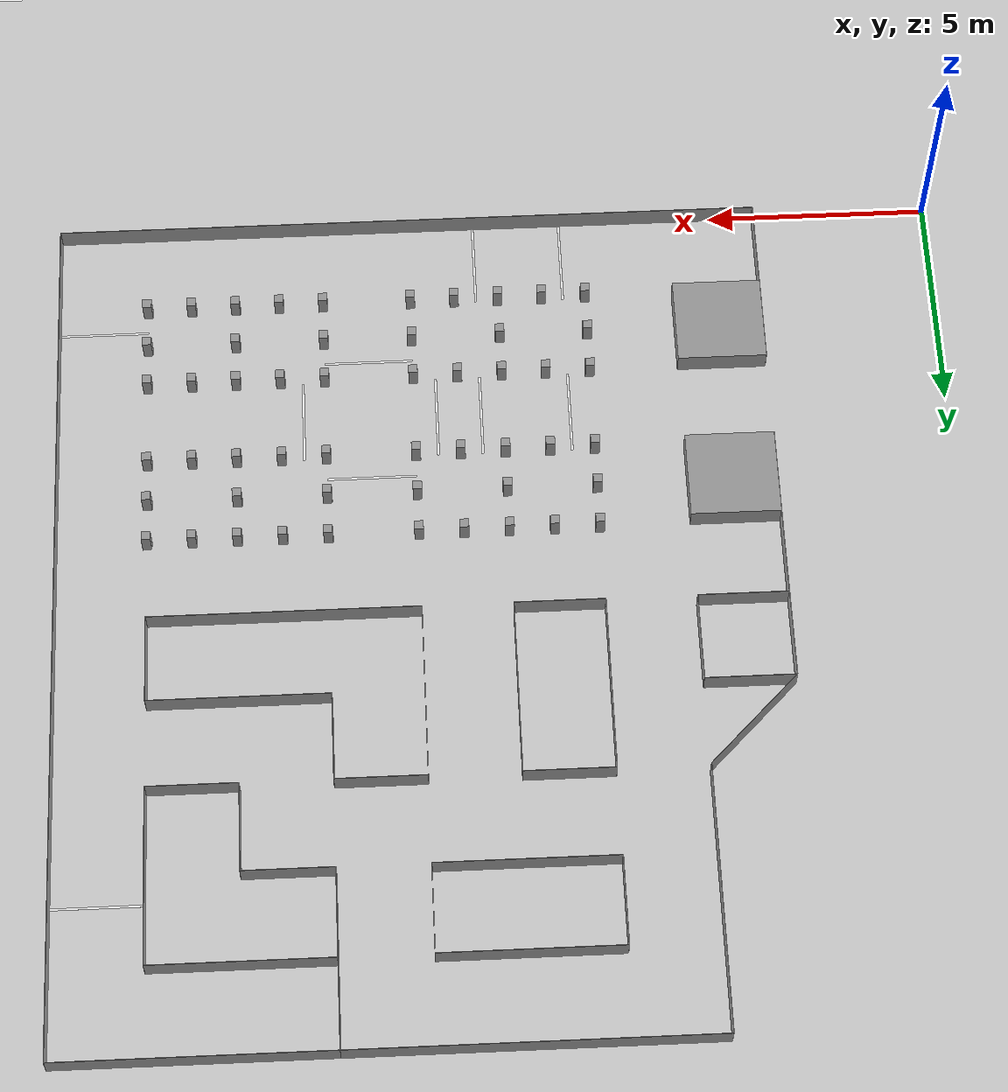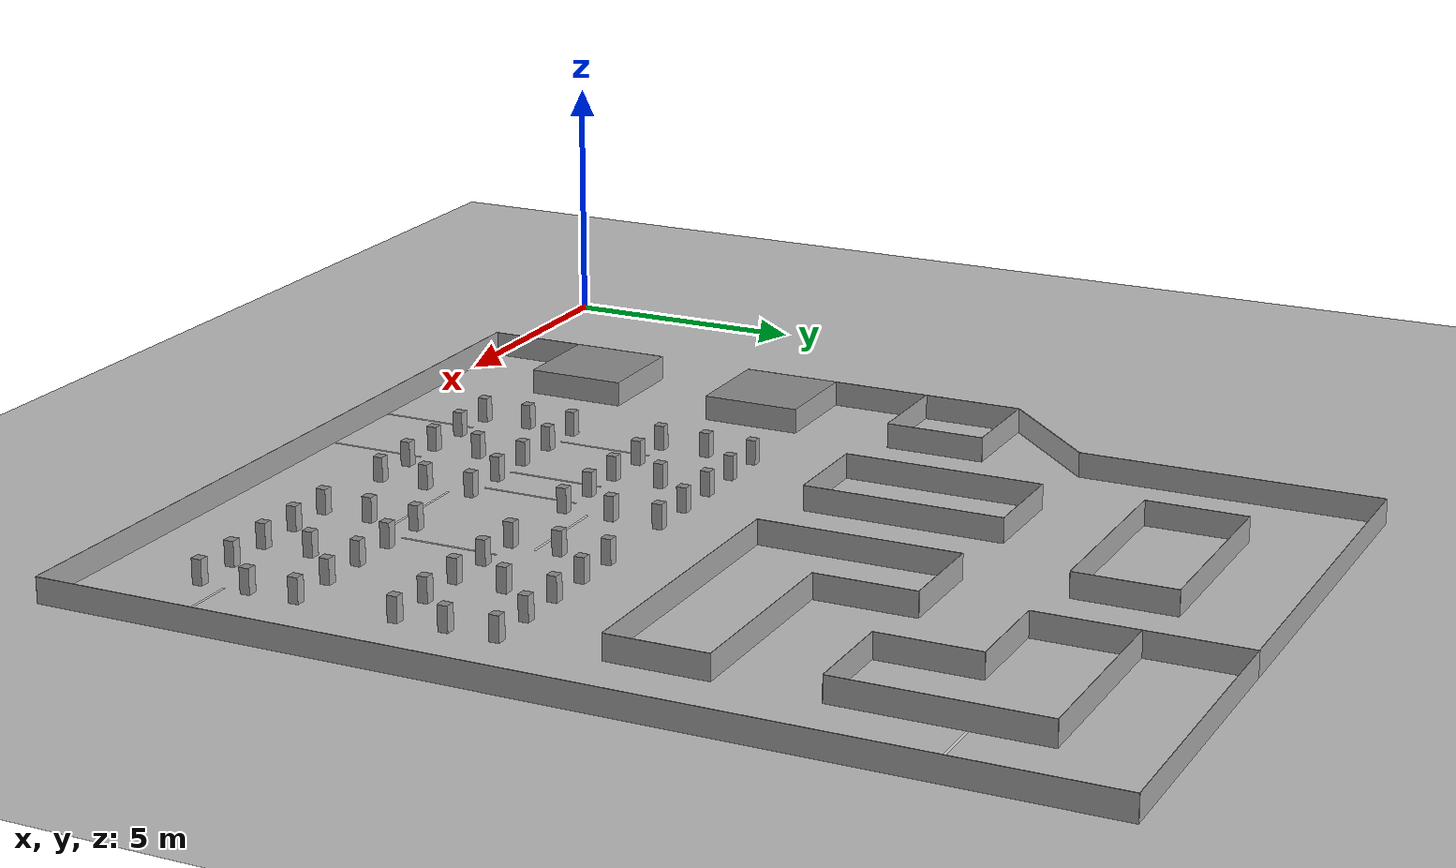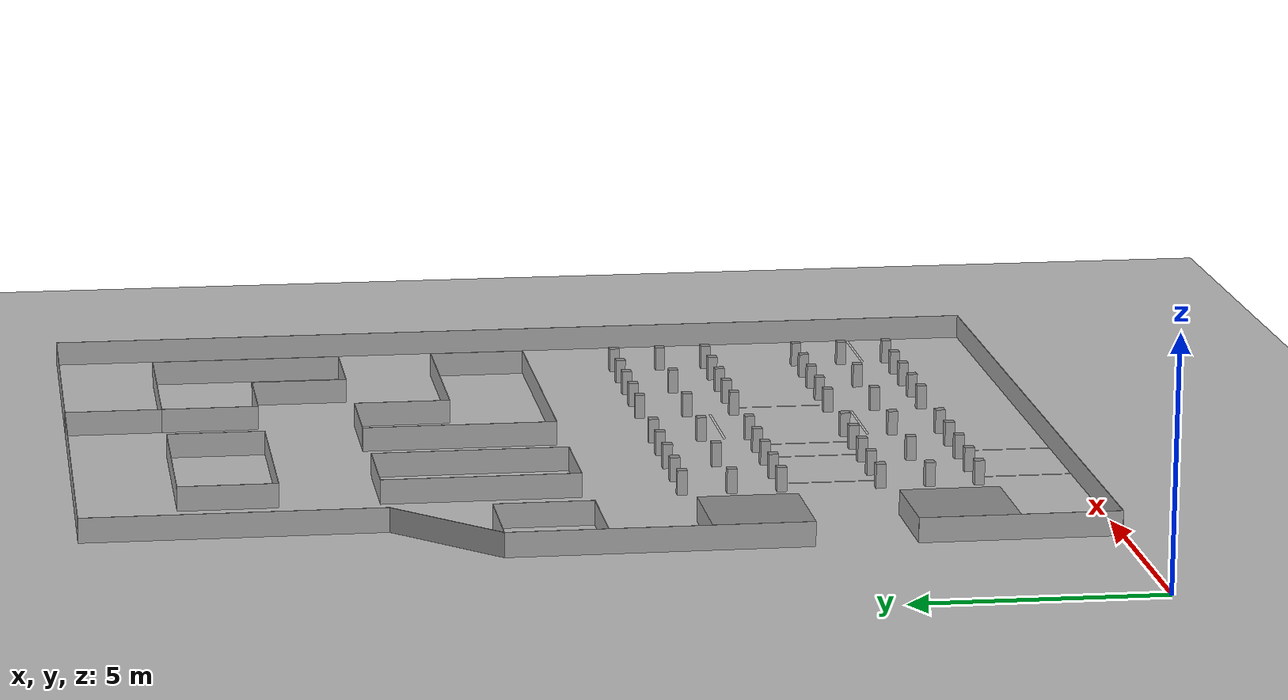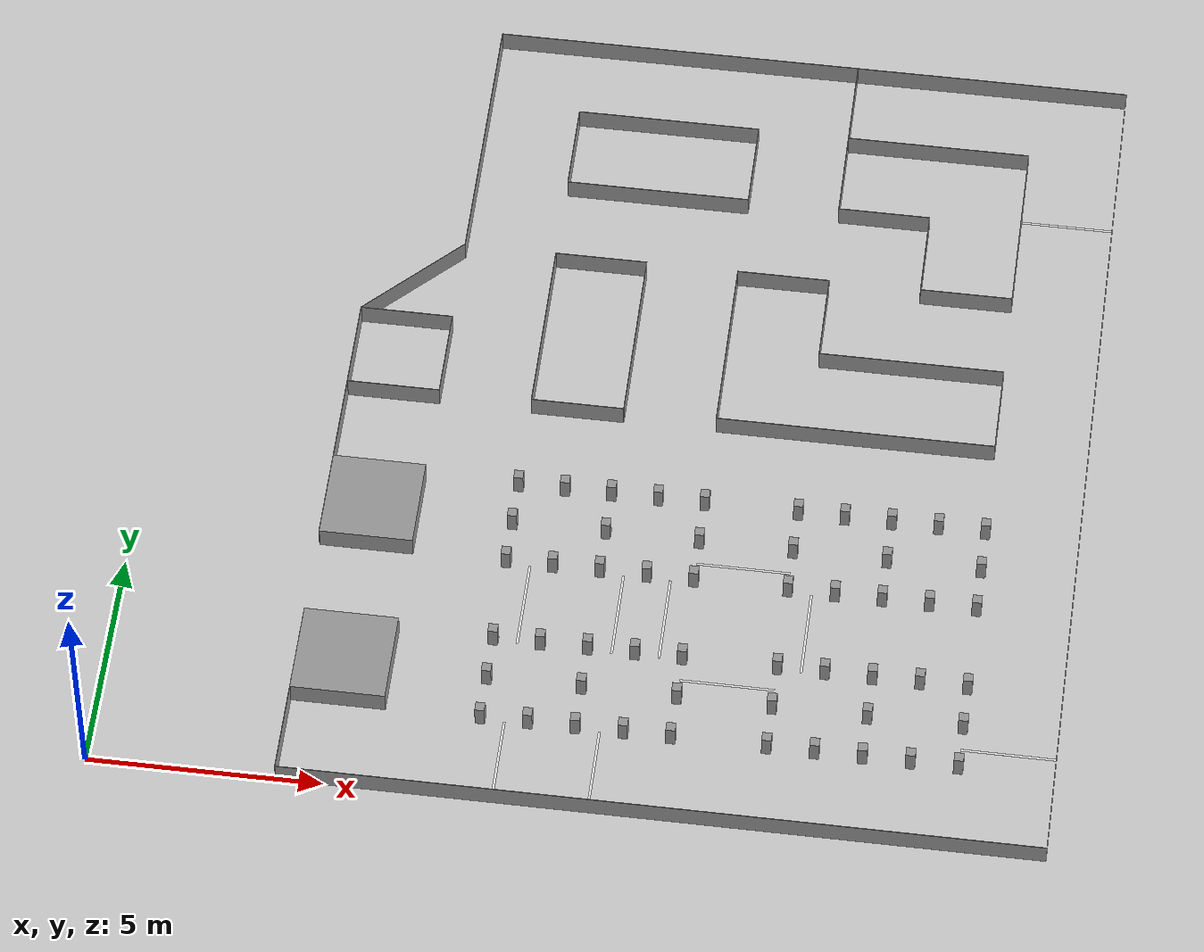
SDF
<sdf version="1.6">
 <world name="default">
  <model name="box_98">
   <pose>5.0 3.0 0.25 0 0 0</pose>
   <link name="link">
    <inertial>
     <mass>1</mass>
     <inertia><ixx>0</ixx><ixy>0</ixy><ixz>0</ixz><iyy>0</iyy><iyz>0</iyz><izz>0</izz></inertia>
    </inertial>
    <collision name="collision"><geometry><box><size>2.0 2.0 0.5</size></box></geometry></collision>
    <visual name="visual">
     <geometry><box><size>2.0 2.0 0.5</size></box></geometry>
     <material>
      <script><name>Gazebo/Grey</name><uri>file://media/materials/scripts/gazebo.material</uri></script>
     </material>
    </visual>
   </link>
   <static>1</static>
  </model>
  <model name="box_97">
   <pose>5.0 7.0 0.25 0 0 0</pose>
   <link name="link">
    <inertial>
     <mass>1</mass>
     <inertia><ixx>0</ixx><ixy>0</ixy><ixz>0</ixz><iyy>0</iyy><iyz>0</iyz><izz>0</izz></inertia>
    </inertial>
    <collision name="collision"><geometry><box><size>2.0 2.0 0.5</size></box></geometry></collision>
    <visual name="visual">
     <geometry><box><size>2.0 2.0 0.5</size></box></geometry>
     <material>
      <script><name>Gazebo/Grey</name><uri>file://media/materials/scripts/gazebo.material</uri></script>
     </material>
    </visual>
   </link>
   <static>1</static>
  </model>
  <model name="box_96">
   <pose>16.0 2.0 0.25 0 0 0</pose>
   <link name="link">
    <inertial>
     <mass>1</mass>
     <inertia><ixx>0</ixx><ixy>0</ixy><ixz>0</ixz><iyy>0</iyy><iyz>0</iyz><izz>0</izz></inertia>
    </inertial>
    <collision name="collision"><geometry><box><size>0.2 0.2 0.5</size></box></geometry></collision>
    <visual name="visual">
     <geometry><box><size>0.2 0.2 0.5</size></box></geometry>
     <material>
      <script><name>Gazebo/Grey</name><uri>file://media/materials/scripts/gazebo.material</uri></script>
     </material>
    </visual>
   </link>
   <static>1</static>
  </model>
  <model name="box_95">
   <pose>15.0 2.0 0.25 0 0 0</pose>
   <link name="link">
    <inertial>
     <mass>1</mass>
     <inertia><ixx>0</ixx><ixy>0</ixy><ixz>0</ixz><iyy>0</iyy><iyz>0</iyz><izz>0</izz></inertia>
    </inertial>
    <collision name="collision"><geometry><box><size>0.2 0.2 0.5</size></box></geometry></collision>
    <visual name="visual">
     <geometry><box><size>0.2 0.2 0.5</size></box></geometry>
     <material>
      <script><name>Gazebo/Grey</name><uri>file://media/materials/scripts/gazebo.material</uri></script>
     </material>
    </visual>
   </link>
   <static>1</static>
  </model>
  <model name="box_94">
   <pose>14.0 2.0 0.25 0 0 0</pose>
   <link name="link">
    <inertial>
     <mass>1</mass>
     <inertia><ixx>0</ixx><ixy>0</ixy><ixz>0</ixz><iyy>0</iyy><iyz>0</iyz><izz>0</izz></inertia>
    </inertial>
    <collision name="collision"><geometry><box><size>0.2 0.2 0.5</size></box></geometry></collision>
    <visual name="visual">
     <geometry><box><size>0.2 0.2 0.5</size></box></geometry>
     <material>
      <script><name>Gazebo/Grey</name><uri>file://media/materials/scripts/gazebo.material</uri></script>
     </material>
    </visual>
   </link>
   <static>1</static>
  </model>
  <model name="box_93">
   <pose>16.0 3.0 0.25 0 0 0</pose>
   <link name="link">
    <inertial>
     <mass>1</mass>
     <inertia><ixx>0</ixx><ixy>0</ixy><ixz>0</ixz><iyy>0</iyy><iyz>0</iyz><izz>0</izz></inertia>
    </inertial>
    <collision name="collision"><geometry><box><size>0.2 0.2 0.5</size></box></geometry></collision>
    <visual name="visual">
     <geometry><box><size>0.2 0.2 0.5</size></box></geometry>
     <material>
      <script><name>Gazebo/Grey</name><uri>file://media/materials/scripts/gazebo.material</uri></script>
     </material>
    </visual>
   </link>
   <static>1</static>
  </model>
  <model name="box_92">
   <pose>14.0 3.0 0.25 0 0 0</pose>
   <link name="link">
    <inertial>
     <mass>1</mass>
     <inertia><ixx>0</ixx><ixy>0</ixy><ixz>0</ixz><iyy>0</iyy><iyz>0</iyz><izz>0</izz></inertia>
    </inertial>
    <collision name="collision"><geometry><box><size>0.2 0.2 0.5</size></box></geometry></collision>
    <visual name="visual">
     <geometry><box><size>0.2 0.2 0.5</size></box></geometry>
     <material>
      <script><name>Gazebo/Grey</name><uri>file://media/materials/scripts/gazebo.material</uri></script>
     </material>
    </visual>
   </link>
   <static>1</static>
  </model>
  <model name="box_91">
   <pose>16.0 4.0 0.25 0 0 0</pose>
   <link name="link">
    <inertial>
     <mass>1</mass>
     <inertia><ixx>0</ixx><ixy>0</ixy><ixz>0</ixz><iyy>0</iyy><iyz>0</iyz><izz>0</izz></inertia>
    </inertial>
    <collision name="collision"><geometry><box><size>0.2 0.2 0.5</size></box></geometry></collision>
    <visual name="visual">
     <geometry><box><size>0.2 0.2 0.5</size></box></geometry>
     <material>
      <script><name>Gazebo/Grey</name><uri>file://media/materials/scripts/gazebo.material</uri></script>
     </material>
    </visual>
   </link>
   <static>1</static>
  </model>
  <model name="box_90">
   <pose>15.0 4.0 0.25 0 0 0</pose>
   <link name="link">
    <inertial>
     <mass>1</mass>
     <inertia><ixx>0</ixx><ixy>0</ixy><ixz>0</ixz><iyy>0</iyy><iyz>0</iyz><izz>0</izz></inertia>
    </inertial>
    <collision name="collision"><geometry><box><size>0.2 0.2 0.5</size></box></geometry></collision>
    <visual name="visual">
     <geometry><box><size>0.2 0.2 0.5</size></box></geometry>
     <material>
      <script><name>Gazebo/Grey</name><uri>file://media/materials/scripts/gazebo.material</uri></script>
     </material>
    </visual>
   </link>
   <static>1</static>
  </model>
  <model name="box_89">
   <pose>14.0 4.0 0.25 0 0 0</pose>
   <link name="link">
    <inertial>
     <mass>1</mass>
     <inertia><ixx>0</ixx><ixy>0</ixy><ixz>0</ixz><iyy>0</iyy><iyz>0</iyz><izz>0</izz></inertia>
    </inertial>
    <collision name="collision"><geometry><box><size>0.2 0.2 0.5</size></box></geometry></collision>
    <visual name="visual">
     <geometry><box><size>0.2 0.2 0.5</size></box></geometry>
     <material>
      <script><name>Gazebo/Grey</name><uri>file://media/materials/scripts/gazebo.material</uri></script>
     </material>
    </visual>
   </link>
   <static>1</static>
  </model>
  <model name="box_88">
   <pose>12.0 2.0 0.25 0 0 0</pose>
   <link name="link">
    <inertial>
     <mass>1</mass>
     <inertia><ixx>0</ixx><ixy>0</ixy><ixz>0</ixz><iyy>0</iyy><iyz>0</iyz><izz>0</izz></inertia>
    </inertial>
    <collision name="collision"><geometry><box><size>0.2 0.2 0.5</size></box></geometry></collision>
    <visual name="visual">
     <geometry><box><size>0.2 0.2 0.5</size></box></geometry>
     <material>
      <script><name>Gazebo/Grey</name><uri>file://media/materials/scripts/gazebo.material</uri></script>
     </material>
    </visual>
   </link>
   <static>1</static>
  </model>
  <model name="box_87">
   <pose>11.0 2.0 0.25 0 0 0</pose>
   <link name="link">
    <inertial>
     <mass>1</mass>
     <inertia><ixx>0</ixx><ixy>0</ixy><ixz>0</ixz><iyy>0</iyy><iyz>0</iyz><izz>0</izz></inertia>
    </inertial>
    <collision name="collision"><geometry><box><size>0.2 0.2 0.5</size></box></geometry></collision>
    <visual name="visual">
     <geometry><box><size>0.2 0.2 0.5</size></box></geometry>
     <material>
      <script><name>Gazebo/Grey</name><uri>file://media/materials/scripts/gazebo.material</uri></script>
     </material>
    </visual>
   </link>
   <static>1</static>
  </model>
  <model name="box_86">
   <pose>10.0 2.0 0.25 0 0 0</pose>
   <link name="link">
    <inertial>
     <mass>1</mass>
     <inertia><ixx>0</ixx><ixy>0</ixy><ixz>0</ixz><iyy>0</iyy><iyz>0</iyz><izz>0</izz></inertia>
    </inertial>
    <collision name="collision"><geometry><box><size>0.2 0.2 0.5</size></box></geometry></collision>
    <visual name="visual">
     <geometry><box><size>0.2 0.2 0.5</size></box></geometry>
     <material>
      <script><name>Gazebo/Grey</name><uri>file://media/materials/scripts/gazebo.material</uri></script>
     </material>
    </visual>
   </link>
   <static>1</static>
  </model>
  <model name="box_85">
   <pose>12.0 3.0 0.25 0 0 0</pose>
   <link name="link">
    <inertial>
     <mass>1</mass>
     <inertia><ixx>0</ixx><ixy>0</ixy><ixz>0</ixz><iyy>0</iyy><iyz>0</iyz><izz>0</izz></inertia>
    </inertial>
    <collision name="collision"><geometry><box><size>0.2 0.2 0.5</size></box></geometry></collision>
    <visual name="visual">
     <geometry><box><size>0.2 0.2 0.5</size></box></geometry>
     <material>
      <script><name>Gazebo/Grey</name><uri>file://media/materials/scripts/gazebo.material</uri></script>
     </material>
    </visual>
   </link>
   <static>1</static>
  </model>
  <model name="box_84">
   <pose>10.0 3.0 0.25 0 0 0</pose>
   <link name="link">
    <inertial>
     <mass>1</mass>
     <inertia><ixx>0</ixx><ixy>0</ixy><ixz>0</ixz><iyy>0</iyy><iyz>0</iyz><izz>0</izz></inertia>
    </inertial>
    <collision name="collision"><geometry><box><size>0.2 0.2 0.5</size></box></geometry></collision>
    <visual name="visual">
     <geometry><box><size>0.2 0.2 0.5</size></box></geometry>
     <material>
      <script><name>Gazebo/Grey</name><uri>file://media/materials/scripts/gazebo.material</uri></script>
     </material>
    </visual>
   </link>
   <static>1</static>
  </model>
  <model name="box_83">
   <pose>12.0 4.0 0.25 0 0 0</pose>
   <link name="link">
    <inertial>
     <mass>1</mass>
     <inertia><ixx>0</ixx><ixy>0</ixy><ixz>0</ixz><iyy>0</iyy><iyz>0</iyz><izz>0</izz></inertia>
    </inertial>
    <collision name="collision"><geometry><box><size>0.2 0.2 0.5</size></box></geometry></collision>
    <visual name="visual">
     <geometry><box><size>0.2 0.2 0.5</size></box></geometry>
     <material>
      <script><name>Gazebo/Grey</name><uri>file://media/materials/scripts/gazebo.material</uri></script>
     </material>
    </visual>
   </link>
   <static>1</static>
  </model>
  <model name="box_82">
   <pose>11.0 4.0 0.25 0 0 0</pose>
   <link name="link">
    <inertial>
     <mass>1</mass>
     <inertia><ixx>0</ixx><ixy>0</ixy><ixz>0</ixz><iyy>0</iyy><iyz>0</iyz><izz>0</izz></inertia>
    </inertial>
    <collision name="collision"><geometry><box><size>0.2 0.2 0.5</size></box></geometry></collision>
    <visual name="visual">
     <geometry><box><size>0.2 0.2 0.5</size></box></geometry>
     <material>
      <script><name>Gazebo/Grey</name><uri>file://media/materials/scripts/gazebo.material</uri></script>
     </material>
    </visual>
   </link>
   <static>1</static>
  </model>
  <model name="box_81">
   <pose>10.0 4.0 0.25 0 0 0</pose>
   <link name="link">
    <inertial>
     <mass>1</mass>
     <inertia><ixx>0</ixx><ixy>0</ixy><ixz>0</ixz><iyy>0</iyy><iyz>0</iyz><izz>0</izz></inertia>
    </inertial>
    <collision name="collision"><geometry><box><size>0.2 0.2 0.5</size></box></geometry></collision>
    <visual name="visual">
     <geometry><box><size>0.2 0.2 0.5</size></box></geometry>
     <material>
      <script><name>Gazebo/Grey</name><uri>file://media/materials/scripts/gazebo.material</uri></script>
     </material>
    </visual>
   </link>
   <static>1</static>
  </model>
  <model name="box_80">
   <pose>12.0 6.0 0.25 0 0 0</pose>
   <link name="link">
    <inertial>
     <mass>1</mass>
     <inertia><ixx>0</ixx><ixy>0</ixy><ixz>0</ixz><iyy>0</iyy><iyz>0</iyz><izz>0</izz></inertia>
    </inertial>
    <collision name="collision"><geometry><box><size>0.2 0.2 0.5</size></box></geometry></collision>
    <visual name="visual">
     <geometry><box><size>0.2 0.2 0.5</size></box></geometry>
     <material>
      <script><name>Gazebo/Grey</name><uri>file://media/materials/scripts/gazebo.material</uri></script>
     </material>
    </visual>
   </link>
   <static>1</static>
  </model>
  <model name="box_79">
   <pose>11.0 6.0 0.25 0 0 0</pose>
   <link name="link">
    <inertial>
     <mass>1</mass>
     <inertia><ixx>0</ixx><ixy>0</ixy><ixz>0</ixz><iyy>0</iyy><iyz>0</iyz><izz>0</izz></inertia>
    </inertial>
    <collision name="collision"><geometry><box><size>0.2 0.2 0.5</size></box></geometry></collision>
    <visual name="visual">
     <geometry><box><size>0.2 0.2 0.5</size></box></geometry>
     <material>
      <script><name>Gazebo/Grey</name><uri>file://media/materials/scripts/gazebo.material</uri></script>
     </material>
    </visual>
   </link>
   <static>1</static>
  </model>
  <model name="box_78">
   <pose>10.0 6.0 0.25 0 0 0</pose>
   <link name="link">
    <inertial>
     <mass>1</mass>
     <inertia><ixx>0</ixx><ixy>0</ixy><ixz>0</ixz><iyy>0</iyy><iyz>0</iyz><izz>0</izz></inertia>
    </inertial>
    <collision name="collision"><geometry><box><size>0.2 0.2 0.5</size></box></geometry></collision>
    <visual name="visual">
     <geometry><box><size>0.2 0.2 0.5</size></box></geometry>
     <material>
      <script><name>Gazebo/Grey</name><uri>file://media/materials/scripts/gazebo.material</uri></script>
     </material>
    </visual>
   </link>
   <static>1</static>
  </model>
  <model name="box_77">
   <pose>12.0 7.0 0.25 0 0 0</pose>
   <link name="link">
    <inertial>
     <mass>1</mass>
     <inertia><ixx>0</ixx><ixy>0</ixy><ixz>0</ixz><iyy>0</iyy><iyz>0</iyz><izz>0</izz></inertia>
    </inertial>
    <collision name="collision"><geometry><box><size>0.2 0.2 0.5</size></box></geometry></collision>
    <visual name="visual">
     <geometry><box><size>0.2 0.2 0.5</size></box></geometry>
     <material>
      <script><name>Gazebo/Grey</name><uri>file://media/materials/scripts/gazebo.material</uri></script>
     </material>
    </visual>
   </link>
   <static>1</static>
  </model>
  <model name="box_76">
   <pose>10.0 7.0 0.25 0 0 0</pose>
   <link name="link">
    <inertial>
     <mass>1</mass>
     <inertia><ixx>0</ixx><ixy>0</ixy><ixz>0</ixz><iyy>0</iyy><iyz>0</iyz><izz>0</izz></inertia>
    </inertial>
    <collision name="collision"><geometry><box><size>0.2 0.2 0.5</size></box></geometry></collision>
    <visual name="visual">
     <geometry><box><size>0.2 0.2 0.5</size></box></geometry>
     <material>
      <script><name>Gazebo/Grey</name><uri>file://media/materials/scripts/gazebo.material</uri></script>
     </material>
    </visual>
   </link>
   <static>1</static>
  </model>
  <model name="box_75">
   <pose>12.0 8.0 0.25 0 0 0</pose>
   <link name="link">
    <inertial>
     <mass>1</mass>
     <inertia><ixx>0</ixx><ixy>0</ixy><ixz>0</ixz><iyy>0</iyy><iyz>0</iyz><izz>0</izz></inertia>
    </inertial>
    <collision name="collision"><geometry><box><size>0.2 0.2 0.5</size></box></geometry></collision>
    <visual name="visual">
     <geometry><box><size>0.2 0.2 0.5</size></box></geometry>
     <material>
      <script><name>Gazebo/Grey</name><uri>file://media/materials/scripts/gazebo.material</uri></script>
     </material>
    </visual>
   </link>
   <static>1</static>
  </model>
  <model name="box_74">
   <pose>11.0 8.0 0.25 0 0 0</pose>
   <link name="link">
    <inertial>
     <mass>1</mass>
     <inertia><ixx>0</ixx><ixy>0</ixy><ixz>0</ixz><iyy>0</iyy><iyz>0</iyz><izz>0</izz></inertia>
    </inertial>
    <collision name="collision"><geometry><box><size>0.2 0.2 0.5</size></box></geometry></collision>
    <visual name="visual">
     <geometry><box><size>0.2 0.2 0.5</size></box></geometry>
     <material>
      <script><name>Gazebo/Grey</name><uri>file://media/materials/scripts/gazebo.material</uri></script>
     </material>
    </visual>
   </link>
   <static>1</static>
  </model>
  <model name="box_73">
   <pose>10.0 8.0 0.25 0 0 0</pose>
   <link name="link">
    <inertial>
     <mass>1</mass>
     <inertia><ixx>0</ixx><ixy>0</ixy><ixz>0</ixz><iyy>0</iyy><iyz>0</iyz><izz>0</izz></inertia>
    </inertial>
    <collision name="collision"><geometry><box><size>0.2 0.2 0.5</size></box></geometry></collision>
    <visual name="visual">
     <geometry><box><size>0.2 0.2 0.5</size></box></geometry>
     <material>
      <script><name>Gazebo/Grey</name><uri>file://media/materials/scripts/gazebo.material</uri></script>
     </material>
    </visual>
   </link>
   <static>1</static>
  </model>
  <model name="box_72">
   <pose>16.0 6.0 0.25 0 0 0</pose>
   <link name="link">
    <inertial>
     <mass>1</mass>
     <inertia><ixx>0</ixx><ixy>0</ixy><ixz>0</ixz><iyy>0</iyy><iyz>0</iyz><izz>0</izz></inertia>
    </inertial>
    <collision name="collision"><geometry><box><size>0.2 0.2 0.5</size></box></geometry></collision>
    <visual name="visual">
     <geometry><box><size>0.2 0.2 0.5</size></box></geometry>
     <material>
      <script><name>Gazebo/Grey</name><uri>file://media/materials/scripts/gazebo.material</uri></script>
     </material>
    </visual>
   </link>
   <static>1</static>
  </model>
  <model name="box_71">
   <pose>15.0 6.0 0.25 0 0 0</pose>
   <link name="link">
    <inertial>
     <mass>1</mass>
     <inertia><ixx>0</ixx><ixy>0</ixy><ixz>0</ixz><iyy>0</iyy><iyz>0</iyz><izz>0</izz></inertia>
    </inertial>
    <collision name="collision"><geometry><box><size>0.2 0.2 0.5</size></box></geometry></collision>
    <visual name="visual">
     <geometry><box><size>0.2 0.2 0.5</size></box></geometry>
     <material>
      <script><name>Gazebo/Grey</name><uri>file://media/materials/scripts/gazebo.material</uri></script>
     </material>
    </visual>
   </link>
   <static>1</static>
  </model>
  <model name="box_70">
   <pose>14.0 6.0 0.25 0 0 0</pose>
   <link name="link">
    <inertial>
     <mass>1</mass>
     <inertia><ixx>0</ixx><ixy>0</ixy><ixz>0</ixz><iyy>0</iyy><iyz>0</iyz><izz>0</izz></inertia>
    </inertial>
    <collision name="collision"><geometry><box><size>0.2 0.2 0.5</size></box></geometry></collision>
    <visual name="visual">
     <geometry><box><size>0.2 0.2 0.5</size></box></geometry>
     <material>
      <script><name>Gazebo/Grey</name><uri>file://media/materials/scripts/gazebo.material</uri></script>
     </material>
    </visual>
   </link>
   <static>1</static>
  </model>
  <model name="box_69">
   <pose>16.0 7.0 0.25 0 0 0</pose>
   <link name="link">
    <inertial>
     <mass>1</mass>
     <inertia><ixx>0</ixx><ixy>0</ixy><ixz>0</ixz><iyy>0</iyy><iyz>0</iyz><izz>0</izz></inertia>
    </inertial>
    <collision name="collision"><geometry><box><size>0.2 0.2 0.5</size></box></geometry></collision>
    <visual name="visual">
     <geometry><box><size>0.2 0.2 0.5</size></box></geometry>
     <material>
      <script><name>Gazebo/Grey</name><uri>file://media/materials/scripts/gazebo.material</uri></script>
     </material>
    </visual>
   </link>
   <static>1</static>
  </model>
  <model name="box_68">
   <pose>14.0 7.0 0.25 0 0 0</pose>
   <link name="link">
    <inertial>
     <mass>1</mass>
     <inertia><ixx>0</ixx><ixy>0</ixy><ixz>0</ixz><iyy>0</iyy><iyz>0</iyz><izz>0</izz></inertia>
    </inertial>
    <collision name="collision"><geometry><box><size>0.2 0.2 0.5</size></box></geometry></collision>
    <visual name="visual">
     <geometry><box><size>0.2 0.2 0.5</size></box></geometry>
     <material>
      <script><name>Gazebo/Grey</name><uri>file://media/materials/scripts/gazebo.material</uri></script>
     </material>
    </visual>
   </link>
   <static>1</static>
  </model>
  <model name="box_67">
   <pose>16.0 8.0 0.25 0 0 0</pose>
   <link name="link">
    <inertial>
     <mass>1</mass>
     <inertia><ixx>0</ixx><ixy>0</ixy><ixz>0</ixz><iyy>0</iyy><iyz>0</iyz><izz>0</izz></inertia>
    </inertial>
    <collision name="collision"><geometry><box><size>0.2 0.2 0.5</size></box></geometry></collision>
    <visual name="visual">
     <geometry><box><size>0.2 0.2 0.5</size></box></geometry>
     <material>
      <script><name>Gazebo/Grey</name><uri>file://media/materials/scripts/gazebo.material</uri></script>
     </material>
    </visual>
   </link>
   <static>1</static>
  </model>
  <model name="box_66">
   <pose>15.0 8.0 0.25 0 0 0</pose>
   <link name="link">
    <inertial>
     <mass>1</mass>
     <inertia><ixx>0</ixx><ixy>0</ixy><ixz>0</ixz><iyy>0</iyy><iyz>0</iyz><izz>0</izz></inertia>
    </inertial>
    <collision name="collision"><geometry><box><size>0.2 0.2 0.5</size></box></geometry></collision>
    <visual name="visual">
     <geometry><box><size>0.2 0.2 0.5</size></box></geometry>
     <material>
      <script><name>Gazebo/Grey</name><uri>file://media/materials/scripts/gazebo.material</uri></script>
     </material>
    </visual>
   </link>
   <static>1</static>
  </model>
  <model name="box_65">
   <pose>14.0 8.0 0.25 0 0 0</pose>
   <link name="link">
    <inertial>
     <mass>1</mass>
     <inertia><ixx>0</ixx><ixy>0</ixy><ixz>0</ixz><iyy>0</iyy><iyz>0</iyz><izz>0</izz></inertia>
    </inertial>
    <collision name="collision"><geometry><box><size>0.2 0.2 0.5</size></box></geometry></collision>
    <visual name="visual">
     <geometry><box><size>0.2 0.2 0.5</size></box></geometry>
     <material>
      <script><name>Gazebo/Grey</name><uri>file://media/materials/scripts/gazebo.material</uri></script>
     </material>
    </visual>
   </link>
   <static>1</static>
  </model>
  <model name="box_64">
   <pose>10.0 2.0 0.25 0 0 0</pose>
   <link name="link">
    <inertial>
     <mass>1</mass>
     <inertia><ixx>0</ixx><ixy>0</ixy><ixz>0</ixz><iyy>0</iyy><iyz>0</iyz><izz>0</izz></inertia>
    </inertial>
    <collision name="collision"><geometry><box><size>0.2 0.2 0.5</size></box></geometry></collision>
    <visual name="visual">
     <geometry><box><size>0.2 0.2 0.5</size></box></geometry>
     <material>
      <script><name>Gazebo/Grey</name><uri>file://media/materials/scripts/gazebo.material</uri></script>
     </material>
    </visual>
   </link>
   <static>1</static>
  </model>
  <model name="box_63">
   <pose>9.0 2.0 0.25 0 0 0</pose>
   <link name="link">
    <inertial>
     <mass>1</mass>
     <inertia><ixx>0</ixx><ixy>0</ixy><ixz>0</ixz><iyy>0</iyy><iyz>0</iyz><izz>0</izz></inertia>
    </inertial>
    <collision name="collision"><geometry><box><size>0.2 0.2 0.5</size></box></geometry></collision>
    <visual name="visual">
     <geometry><box><size>0.2 0.2 0.5</size></box></geometry>
     <material>
      <script><name>Gazebo/Grey</name><uri>file://media/materials/scripts/gazebo.material</uri></script>
     </material>
    </visual>
   </link>
   <static>1</static>
  </model>
  <model name="box_62">
   <pose>8.0 2.0 0.25 0 0 0</pose>
   <link name="link">
    <inertial>
     <mass>1</mass>
     <inertia><ixx>0</ixx><ixy>0</ixy><ixz>0</ixz><iyy>0</iyy><iyz>0</iyz><izz>0</izz></inertia>
    </inertial>
    <collision name="collision"><geometry><box><size>0.2 0.2 0.5</size></box></geometry></collision>
    <visual name="visual">
     <geometry><box><size>0.2 0.2 0.5</size></box></geometry>
     <material>
      <script><name>Gazebo/Grey</name><uri>file://media/materials/scripts/gazebo.material</uri></script>
     </material>
    </visual>
   </link>
   <static>1</static>
  </model>
  <model name="box_61">
   <pose>10.0 3.0 0.25 0 0 0</pose>
   <link name="link">
    <inertial>
     <mass>1</mass>
     <inertia><ixx>0</ixx><ixy>0</ixy><ixz>0</ixz><iyy>0</iyy><iyz>0</iyz><izz>0</izz></inertia>
    </inertial>
    <collision name="collision"><geometry><box><size>0.2 0.2 0.5</size></box></geometry></collision>
    <visual name="visual">
     <geometry><box><size>0.2 0.2 0.5</size></box></geometry>
     <material>
      <script><name>Gazebo/Grey</name><uri>file://media/materials/scripts/gazebo.material</uri></script>
     </material>
    </visual>
   </link>
   <static>1</static>
  </model>
  <model name="box_60">
   <pose>8.0 3.0 0.25 0 0 0</pose>
   <link name="link">
    <inertial>
     <mass>1</mass>
     <inertia><ixx>0</ixx><ixy>0</ixy><ixz>0</ixz><iyy>0</iyy><iyz>0</iyz><izz>0</izz></inertia>
    </inertial>
    <collision name="collision"><geometry><box><size>0.2 0.2 0.5</size></box></geometry></collision>
    <visual name="visual">
     <geometry><box><size>0.2 0.2 0.5</size></box></geometry>
     <material>
      <script><name>Gazebo/Grey</name><uri>file://media/materials/scripts/gazebo.material</uri></script>
     </material>
    </visual>
   </link>
   <static>1</static>
  </model>
  <model name="box_59">
   <pose>10.0 4.0 0.25 0 0 0</pose>
   <link name="link">
    <inertial>
     <mass>1</mass>
     <inertia><ixx>0</ixx><ixy>0</ixy><ixz>0</ixz><iyy>0</iyy><iyz>0</iyz><izz>0</izz></inertia>
    </inertial>
    <collision name="collision"><geometry><box><size>0.2 0.2 0.5</size></box></geometry></collision>
    <visual name="visual">
     <geometry><box><size>0.2 0.2 0.5</size></box></geometry>
     <material>
      <script><name>Gazebo/Grey</name><uri>file://media/materials/scripts/gazebo.material</uri></script>
     </material>
    </visual>
   </link>
   <static>1</static>
  </model>
  <model name="box_58">
   <pose>9.0 4.0 0.25 0 0 0</pose>
   <link name="link">
    <inertial>
     <mass>1</mass>
     <inertia><ixx>0</ixx><ixy>0</ixy><ixz>0</ixz><iyy>0</iyy><iyz>0</iyz><izz>0</izz></inertia>
    </inertial>
    <collision name="collision"><geometry><box><size>0.2 0.2 0.5</size></box></geometry></collision>
    <visual name="visual">
     <geometry><box><size>0.2 0.2 0.5</size></box></geometry>
     <material>
      <script><name>Gazebo/Grey</name><uri>file://media/materials/scripts/gazebo.material</uri></script>
     </material>
    </visual>
   </link>
   <static>1</static>
  </model>
  <model name="box_57">
   <pose>8.0 4.0 0.25 0 0 0</pose>
   <link name="link">
    <inertial>
     <mass>1</mass>
     <inertia><ixx>0</ixx><ixy>0</ixy><ixz>0</ixz><iyy>0</iyy><iyz>0</iyz><izz>0</izz></inertia>
    </inertial>
    <collision name="collision"><geometry><box><size>0.2 0.2 0.5</size></box></geometry></collision>
    <visual name="visual">
     <geometry><box><size>0.2 0.2 0.5</size></box></geometry>
     <material>
      <script><name>Gazebo/Grey</name><uri>file://media/materials/scripts/gazebo.material</uri></script>
     </material>
    </visual>
   </link>
   <static>1</static>
  </model>
  <model name="box_56">
   <pose>18.0 2.0 0.25 0 0 0</pose>
   <link name="link">
    <inertial>
     <mass>1</mass>
     <inertia><ixx>0</ixx><ixy>0</ixy><ixz>0</ixz><iyy>0</iyy><iyz>0</iyz><izz>0</izz></inertia>
    </inertial>
    <collision name="collision"><geometry><box><size>0.2 0.2 0.5</size></box></geometry></collision>
    <visual name="visual">
     <geometry><box><size>0.2 0.2 0.5</size></box></geometry>
     <material>
      <script><name>Gazebo/Grey</name><uri>file://media/materials/scripts/gazebo.material</uri></script>
     </material>
    </visual>
   </link>
   <static>1</static>
  </model>
  <model name="box_55">
   <pose>17.0 2.0 0.25 0 0 0</pose>
   <link name="link">
    <inertial>
     <mass>1</mass>
     <inertia><ixx>0</ixx><ixy>0</ixy><ixz>0</ixz><iyy>0</iyy><iyz>0</iyz><izz>0</izz></inertia>
    </inertial>
    <collision name="collision"><geometry><box><size>0.2 0.2 0.5</size></box></geometry></collision>
    <visual name="visual">
     <geometry><box><size>0.2 0.2 0.5</size></box></geometry>
     <material>
      <script><name>Gazebo/Grey</name><uri>file://media/materials/scripts/gazebo.material</uri></script>
     </material>
    </visual>
   </link>
   <static>1</static>
  </model>
  <model name="box_54">
   <pose>16.0 2.0 0.25 0 0 0</pose>
   <link name="link">
    <inertial>
     <mass>1</mass>
     <inertia><ixx>0</ixx><ixy>0</ixy><ixz>0</ixz><iyy>0</iyy><iyz>0</iyz><izz>0</izz></inertia>
    </inertial>
    <collision name="collision"><geometry><box><size>0.2 0.2 0.5</size></box></geometry></collision>
    <visual name="visual">
     <geometry><box><size>0.2 0.2 0.5</size></box></geometry>
     <material>
      <script><name>Gazebo/Grey</name><uri>file://media/materials/scripts/gazebo.material</uri></script>
     </material>
    </visual>
   </link>
   <static>1</static>
  </model>
  <model name="box_53">
   <pose>18.0 3.0 0.25 0 0 0</pose>
   <link name="link">
    <inertial>
     <mass>1</mass>
     <inertia><ixx>0</ixx><ixy>0</ixy><ixz>0</ixz><iyy>0</iyy><iyz>0</iyz><izz>0</izz></inertia>
    </inertial>
    <collision name="collision"><geometry><box><size>0.2 0.2 0.5</size></box></geometry></collision>
    <visual name="visual">
     <geometry><box><size>0.2 0.2 0.5</size></box></geometry>
     <material>
      <script><name>Gazebo/Grey</name><uri>file://media/materials/scripts/gazebo.material</uri></script>
     </material>
    </visual>
   </link>
   <static>1</static>
  </model>
  <model name="box_52">
   <pose>16.0 3.0 0.25 0 0 0</pose>
   <link name="link">
    <inertial>
     <mass>1</mass>
     <inertia><ixx>0</ixx><ixy>0</ixy><ixz>0</ixz><iyy>0</iyy><iyz>0</iyz><izz>0</izz></inertia>
    </inertial>
    <collision name="collision"><geometry><box><size>0.2 0.2 0.5</size></box></geometry></collision>
    <visual name="visual">
     <geometry><box><size>0.2 0.2 0.5</size></box></geometry>
     <material>
      <script><name>Gazebo/Grey</name><uri>file://media/materials/scripts/gazebo.material</uri></script>
     </material>
    </visual>
   </link>
   <static>1</static>
  </model>
  <model name="box_51">
   <pose>18.0 4.0 0.25 0 0 0</pose>
   <link name="link">
    <inertial>
     <mass>1</mass>
     <inertia><ixx>0</ixx><ixy>0</ixy><ixz>0</ixz><iyy>0</iyy><iyz>0</iyz><izz>0</izz></inertia>
    </inertial>
    <collision name="collision"><geometry><box><size>0.2 0.2 0.5</size></box></geometry></collision>
    <visual name="visual">
     <geometry><box><size>0.2 0.2 0.5</size></box></geometry>
     <material>
      <script><name>Gazebo/Grey</name><uri>file://media/materials/scripts/gazebo.material</uri></script>
     </material>
    </visual>
   </link>
   <static>1</static>
  </model>
  <model name="box_50">
   <pose>17.0 4.0 0.25 0 0 0</pose>
   <link name="link">
    <inertial>
     <mass>1</mass>
     <inertia><ixx>0</ixx><ixy>0</ixy><ixz>0</ixz><iyy>0</iyy><iyz>0</iyz><izz>0</izz></inertia>
    </inertial>
    <collision name="collision"><geometry><box><size>0.2 0.2 0.5</size></box></geometry></collision>
    <visual name="visual">
     <geometry><box><size>0.2 0.2 0.5</size></box></geometry>
     <material>
      <script><name>Gazebo/Grey</name><uri>file://media/materials/scripts/gazebo.material</uri></script>
     </material>
    </visual>
   </link>
   <static>1</static>
  </model>
  <model name="box_49">
   <pose>16.0 4.0 0.25 0 0 0</pose>
   <link name="link">
    <inertial>
     <mass>1</mass>
     <inertia><ixx>0</ixx><ixy>0</ixy><ixz>0</ixz><iyy>0</iyy><iyz>0</iyz><izz>0</izz></inertia>
    </inertial>
    <collision name="collision"><geometry><box><size>0.2 0.2 0.5</size></box></geometry></collision>
    <visual name="visual">
     <geometry><box><size>0.2 0.2 0.5</size></box></geometry>
     <material>
      <script><name>Gazebo/Grey</name><uri>file://media/materials/scripts/gazebo.material</uri></script>
     </material>
    </visual>
   </link>
   <static>1</static>
  </model>
  <model name="box_48">
   <pose>18.0 6.0 0.25 0 0 0</pose>
   <link name="link">
    <inertial>
     <mass>1</mass>
     <inertia><ixx>0</ixx><ixy>0</ixy><ixz>0</ixz><iyy>0</iyy><iyz>0</iyz><izz>0</izz></inertia>
    </inertial>
    <collision name="collision"><geometry><box><size>0.2 0.2 0.5</size></box></geometry></collision>
    <visual name="visual">
     <geometry><box><size>0.2 0.2 0.5</size></box></geometry>
     <material>
      <script><name>Gazebo/Grey</name><uri>file://media/materials/scripts/gazebo.material</uri></script>
     </material>
    </visual>
   </link>
   <static>1</static>
  </model>
  <model name="box_47">
   <pose>17.0 6.0 0.25 0 0 0</pose>
   <link name="link">
    <inertial>
     <mass>1</mass>
     <inertia><ixx>0</ixx><ixy>0</ixy><ixz>0</ixz><iyy>0</iyy><iyz>0</iyz><izz>0</izz></inertia>
    </inertial>
    <collision name="collision"><geometry><box><size>0.2 0.2 0.5</size></box></geometry></collision>
    <visual name="visual">
     <geometry><box><size>0.2 0.2 0.5</size></box></geometry>
     <material>
      <script><name>Gazebo/Grey</name><uri>file://media/materials/scripts/gazebo.material</uri></script>
     </material>
    </visual>
   </link>
   <static>1</static>
  </model>
  <model name="box_46">
   <pose>16.0 6.0 0.25 0 0 0</pose>
   <link name="link">
    <inertial>
     <mass>1</mass>
     <inertia><ixx>0</ixx><ixy>0</ixy><ixz>0</ixz><iyy>0</iyy><iyz>0</iyz><izz>0</izz></inertia>
    </inertial>
    <collision name="collision"><geometry><box><size>0.2 0.2 0.5</size></box></geometry></collision>
    <visual name="visual">
     <geometry><box><size>0.2 0.2 0.5</size></box></geometry>
     <material>
      <script><name>Gazebo/Grey</name><uri>file://media/materials/scripts/gazebo.material</uri></script>
     </material>
    </visual>
   </link>
   <static>1</static>
  </model>
  <model name="box_45">
   <pose>18.0 7.0 0.25 0 0 0</pose>
   <link name="link">
    <inertial>
     <mass>1</mass>
     <inertia><ixx>0</ixx><ixy>0</ixy><ixz>0</ixz><iyy>0</iyy><iyz>0</iyz><izz>0</izz></inertia>
    </inertial>
    <collision name="collision"><geometry><box><size>0.2 0.2 0.5</size></box></geometry></collision>
    <visual name="visual">
     <geometry><box><size>0.2 0.2 0.5</size></box></geometry>
     <material>
      <script><name>Gazebo/Grey</name><uri>file://media/materials/scripts/gazebo.material</uri></script>
     </material>
    </visual>
   </link>
   <static>1</static>
  </model>
  <model name="box_44">
   <pose>16.0 7.0 0.25 0 0 0</pose>
   <link name="link">
    <inertial>
     <mass>1</mass>
     <inertia><ixx>0</ixx><ixy>0</ixy><ixz>0</ixz><iyy>0</iyy><iyz>0</iyz><izz>0</izz></inertia>
    </inertial>
    <collision name="collision"><geometry><box><size>0.2 0.2 0.5</size></box></geometry></collision>
    <visual name="visual">
     <geometry><box><size>0.2 0.2 0.5</size></box></geometry>
     <material>
      <script><name>Gazebo/Grey</name><uri>file://media/materials/scripts/gazebo.material</uri></script>
     </material>
    </visual>
   </link>
   <static>1</static>
  </model>
  <model name="box_43">
   <pose>18.0 8.0 0.25 0 0 0</pose>
   <link name="link">
    <inertial>
     <mass>1</mass>
     <inertia><ixx>0</ixx><ixy>0</ixy><ixz>0</ixz><iyy>0</iyy><iyz>0</iyz><izz>0</izz></inertia>
    </inertial>
    <collision name="collision"><geometry><box><size>0.2 0.2 0.5</size></box></geometry></collision>
    <visual name="visual">
     <geometry><box><size>0.2 0.2 0.5</size></box></geometry>
     <material>
      <script><name>Gazebo/Grey</name><uri>file://media/materials/scripts/gazebo.material</uri></script>
     </material>
    </visual>
   </link>
   <static>1</static>
  </model>
  <model name="box_42">
   <pose>17.0 8.0 0.25 0 0 0</pose>
   <link name="link">
    <inertial>
     <mass>1</mass>
     <inertia><ixx>0</ixx><ixy>0</ixy><ixz>0</ixz><iyy>0</iyy><iyz>0</iyz><izz>0</izz></inertia>
    </inertial>
    <collision name="collision"><geometry><box><size>0.2 0.2 0.5</size></box></geometry></collision>
    <visual name="visual">
     <geometry><box><size>0.2 0.2 0.5</size></box></geometry>
     <material>
      <script><name>Gazebo/Grey</name><uri>file://media/materials/scripts/gazebo.material</uri></script>
     </material>
    </visual>
   </link>
   <static>1</static>
  </model>
  <model name="box_41">
   <pose>16.0 8.0 0.25 0 0 0</pose>
   <link name="link">
    <inertial>
     <mass>1</mass>
     <inertia><ixx>0</ixx><ixy>0</ixy><ixz>0</ixz><iyy>0</iyy><iyz>0</iyz><izz>0</izz></inertia>
    </inertial>
    <collision name="collision"><geometry><box><size>0.2 0.2 0.5</size></box></geometry></collision>
    <visual name="visual">
     <geometry><box><size>0.2 0.2 0.5</size></box></geometry>
     <material>
      <script><name>Gazebo/Grey</name><uri>file://media/materials/scripts/gazebo.material</uri></script>
     </material>
    </visual>
   </link>
   <static>1</static>
  </model>
  <model name="box_40">
   <pose>10.0 6.0 0.25 0 0 0</pose>
   <link name="link">
    <inertial>
     <mass>1</mass>
     <inertia><ixx>0</ixx><ixy>0</ixy><ixz>0</ixz><iyy>0</iyy><iyz>0</iyz><izz>0</izz></inertia>
    </inertial>
    <collision name="collision"><geometry><box><size>0.2 0.2 0.5</size></box></geometry></collision>
    <visual name="visual">
     <geometry><box><size>0.2 0.2 0.5</size></box></geometry>
     <material>
      <script><name>Gazebo/Grey</name><uri>file://media/materials/scripts/gazebo.material</uri></script>
     </material>
    </visual>
   </link>
   <static>1</static>
  </model>
  <model name="box_39">
   <pose>9.0 6.0 0.25 0 0 0</pose>
   <link name="link">
    <inertial>
     <mass>1</mass>
     <inertia><ixx>0</ixx><ixy>0</ixy><ixz>0</ixz><iyy>0</iyy><iyz>0</iyz><izz>0</izz></inertia>
    </inertial>
    <collision name="collision"><geometry><box><size>0.2 0.2 0.5</size></box></geometry></collision>
    <visual name="visual">
     <geometry><box><size>0.2 0.2 0.5</size></box></geometry>
     <material>
      <script><name>Gazebo/Grey</name><uri>file://media/materials/scripts/gazebo.material</uri></script>
     </material>
    </visual>
   </link>
   <static>1</static>
  </model>
  <model name="box_38">
   <pose>8.0 6.0 0.25 0 0 0</pose>
   <link name="link">
    <inertial>
     <mass>1</mass>
     <inertia><ixx>0</ixx><ixy>0</ixy><ixz>0</ixz><iyy>0</iyy><iyz>0</iyz><izz>0</izz></inertia>
    </inertial>
    <collision name="collision"><geometry><box><size>0.2 0.2 0.5</size></box></geometry></collision>
    <visual name="visual">
     <geometry><box><size>0.2 0.2 0.5</size></box></geometry>
     <material>
      <script><name>Gazebo/Grey</name><uri>file://media/materials/scripts/gazebo.material</uri></script>
     </material>
    </visual>
   </link>
   <static>1</static>
  </model>
  <model name="box_37">
   <pose>10.0 7.0 0.25 0 0 0</pose>
   <link name="link">
    <inertial>
     <mass>1</mass>
     <inertia><ixx>0</ixx><ixy>0</ixy><ixz>0</ixz><iyy>0</iyy><iyz>0</iyz><izz>0</izz></inertia>
    </inertial>
    <collision name="collision"><geometry><box><size>0.2 0.2 0.5</size></box></geometry></collision>
    <visual name="visual">
     <geometry><box><size>0.2 0.2 0.5</size></box></geometry>
     <material>
      <script><name>Gazebo/Grey</name><uri>file://media/materials/scripts/gazebo.material</uri></script>
     </material>
    </visual>
   </link>
   <static>1</static>
  </model>
  <model name="box_36">
   <pose>8.0 7.0 0.25 0 0 0</pose>
   <link name="link">
    <inertial>
     <mass>1</mass>
     <inertia><ixx>0</ixx><ixy>0</ixy><ixz>0</ixz><iyy>0</iyy><iyz>0</iyz><izz>0</izz></inertia>
    </inertial>
    <collision name="collision"><geometry><box><size>0.2 0.2 0.5</size></box></geometry></collision>
    <visual name="visual">
     <geometry><box><size>0.2 0.2 0.5</size></box></geometry>
     <material>
      <script><name>Gazebo/Grey</name><uri>file://media/materials/scripts/gazebo.material</uri></script>
     </material>
    </visual>
   </link>
   <static>1</static>
  </model>
  <model name="box_35">
   <pose>10.0 8.0 0.25 0 0 0</pose>
   <link name="link">
    <inertial>
     <mass>1</mass>
     <inertia><ixx>0</ixx><ixy>0</ixy><ixz>0</ixz><iyy>0</iyy><iyz>0</iyz><izz>0</izz></inertia>
    </inertial>
    <collision name="collision"><geometry><box><size>0.2 0.2 0.5</size></box></geometry></collision>
    <visual name="visual">
     <geometry><box><size>0.2 0.2 0.5</size></box></geometry>
     <material>
      <script><name>Gazebo/Grey</name><uri>file://media/materials/scripts/gazebo.material</uri></script>
     </material>
    </visual>
   </link>
   <static>1</static>
  </model>
  <model name="box_34">
   <pose>9.0 8.0 0.25 0 0 0</pose>
   <link name="link">
    <inertial>
     <mass>1</mass>
     <inertia><ixx>0</ixx><ixy>0</ixy><ixz>0</ixz><iyy>0</iyy><iyz>0</iyz><izz>0</izz></inertia>
    </inertial>
    <collision name="collision"><geometry><box><size>0.2 0.2 0.5</size></box></geometry></collision>
    <visual name="visual">
     <geometry><box><size>0.2 0.2 0.5</size></box></geometry>
     <material>
      <script><name>Gazebo/Grey</name><uri>file://media/materials/scripts/gazebo.material</uri></script>
     </material>
    </visual>
   </link>
   <static>1</static>
  </model>
  <model name="box_33">
   <pose>8.0 8.0 0.25 0 0 0</pose>
   <link name="link">
    <inertial>
     <mass>1</mass>
     <inertia><ixx>0</ixx><ixy>0</ixy><ixz>0</ixz><iyy>0</iyy><iyz>0</iyz><izz>0</izz></inertia>
    </inertial>
    <collision name="collision"><geometry><box><size>0.2 0.2 0.5</size></box></geometry></collision>
    <visual name="visual">
     <geometry><box><size>0.2 0.2 0.5</size></box></geometry>
     <material>
      <script><name>Gazebo/Grey</name><uri>file://media/materials/scripts/gazebo.material</uri></script>
     </material>
    </visual>
   </link>
   <static>1</static>
  </model>
  <model name="box_32">
   <pose>5.0 10.0 0.25 0 0 -0.0</pose>
   <link name="link">
    <inertial>
     <mass>1</mass>
     <inertia><ixx>0</ixx><ixy>0</ixy><ixz>0</ixz><iyy>0</iyy><iyz>0</iyz><izz>0</izz></inertia>
    </inertial>
    <collision name="collision"><geometry><box><size>2.0 0.01 0.5</size></box></geometry></collision>
    <visual name="visual">
     <geometry><box><size>2.0 0.01 0.5</size></box></geometry>
     <material>
      <script><name>Gazebo/Grey</name><uri>file://media/materials/scripts/gazebo.material</uri></script>
     </material>
    </visual>
   </link>
   <static>1</static>
  </model>
  <model name="box_31">
   <pose>6.0 11.0 0.25 0 0 1.5707963267948966</pose>
   <link name="link">
    <inertial>
     <mass>1</mass>
     <inertia><ixx>0</ixx><ixy>0</ixy><ixz>0</ixz><iyy>0</iyy><iyz>0</iyz><izz>0</izz></inertia>
    </inertial>
    <collision name="collision"><geometry><box><size>2.0 0.01 0.5</size></box></geometry></collision>
    <visual name="visual">
     <geometry><box><size>2.0 0.01 0.5</size></box></geometry>
     <material>
      <script><name>Gazebo/Grey</name><uri>file://media/materials/scripts/gazebo.material</uri></script>
     </material>
    </visual>
   </link>
   <static>1</static>
  </model>
  <model name="box_30">
   <pose>5.0 12.0 0.25 0 0 -3.141592653589793</pose>
   <link name="link">
    <inertial>
     <mass>1</mass>
     <inertia><ixx>0</ixx><ixy>0</ixy><ixz>0</ixz><iyy>0</iyy><iyz>0</iyz><izz>0</izz></inertia>
    </inertial>
    <collision name="collision"><geometry><box><size>2.0 0.01 0.5</size></box></geometry></collision>
    <visual name="visual">
     <geometry><box><size>2.0 0.01 0.5</size></box></geometry>
     <material>
      <script><name>Gazebo/Grey</name><uri>file://media/materials/scripts/gazebo.material</uri></script>
     </material>
    </visual>
   </link>
   <static>1</static>
  </model>
  <model name="box_29">
   <pose>10.0 18.0 0.25 0 0 -0.0</pose>
   <link name="link">
    <inertial>
     <mass>1</mass>
     <inertia><ixx>0</ixx><ixy>0</ixy><ixz>0</ixz><iyy>0</iyy><iyz>0</iyz><izz>0</izz></inertia>
    </inertial>
    <collision name="collision"><geometry><box><size>4.0 0.01 0.5</size></box></geometry></collision>
    <visual name="visual">
     <geometry><box><size>4.0 0.01 0.5</size></box></geometry>
     <material>
      <script><name>Gazebo/Grey</name><uri>file://media/materials/scripts/gazebo.material</uri></script>
     </material>
    </visual>
   </link>
   <static>1</static>
  </model>
  <model name="box_28">
   <pose>12.0 17.0 0.25 0 0 -1.5707963267948966</pose>
   <link name="link">
    <inertial>
     <mass>1</mass>
     <inertia><ixx>0</ixx><ixy>0</ixy><ixz>0</ixz><iyy>0</iyy><iyz>0</iyz><izz>0</izz></inertia>
    </inertial>
    <collision name="collision"><geometry><box><size>2.0 0.01 0.5</size></box></geometry></collision>
    <visual name="visual">
     <geometry><box><size>2.0 0.01 0.5</size></box></geometry>
     <material>
      <script><name>Gazebo/Grey</name><uri>file://media/materials/scripts/gazebo.material</uri></script>
     </material>
    </visual>
   </link>
   <static>1</static>
  </model>
  <model name="box_27">
   <pose>10.0 16.0 0.25 0 0 -3.141592653589793</pose>
   <link name="link">
    <inertial>
     <mass>1</mass>
     <inertia><ixx>0</ixx><ixy>0</ixy><ixz>0</ixz><iyy>0</iyy><iyz>0</iyz><izz>0</izz></inertia>
    </inertial>
    <collision name="collision"><geometry><box><size>4.0 0.01 0.5</size></box></geometry></collision>
    <visual name="visual">
     <geometry><box><size>4.0 0.01 0.5</size></box></geometry>
     <material>
      <script><name>Gazebo/Grey</name><uri>file://media/materials/scripts/gazebo.material</uri></script>
     </material>
    </visual>
   </link>
   <static>1</static>
  </model>
  <model name="box_26">
   <pose>8.0 17.0 0.25 0 0 1.5707963267948966</pose>
   <link name="link">
    <inertial>
     <mass>1</mass>
     <inertia><ixx>0</ixx><ixy>0</ixy><ixz>0</ixz><iyy>0</iyy><iyz>0</iyz><izz>0</izz></inertia>
    </inertial>
    <collision name="collision"><geometry><box><size>2.0 0.01 0.5</size></box></geometry></collision>
    <visual name="visual">
     <geometry><box><size>2.0 0.01 0.5</size></box></geometry>
     <material>
      <script><name>Gazebo/Grey</name><uri>file://media/materials/scripts/gazebo.material</uri></script>
     </material>
    </visual>
   </link>
   <static>1</static>
  </model>
  <model name="box_25">
   <pose>9.0 14.0 0.25 0 0 -0.0</pose>
   <link name="link">
    <inertial>
     <mass>1</mass>
     <inertia><ixx>0</ixx><ixy>0</ixy><ixz>0</ixz><iyy>0</iyy><iyz>0</iyz><izz>0</izz></inertia>
    </inertial>
    <collision name="collision"><geometry><box><size>2.0 0.01 0.5</size></box></geometry></collision>
    <visual name="visual">
     <geometry><box><size>2.0 0.01 0.5</size></box></geometry>
     <material>
      <script><name>Gazebo/Grey</name><uri>file://media/materials/scripts/gazebo.material</uri></script>
     </material>
    </visual>
   </link>
   <static>1</static>
  </model>
  <model name="box_24">
   <pose>10.0 12.0 0.25 0 0 -1.5707963267948966</pose>
   <link name="link">
    <inertial>
     <mass>1</mass>
     <inertia><ixx>0</ixx><ixy>0</ixy><ixz>0</ixz><iyy>0</iyy><iyz>0</iyz><izz>0</izz></inertia>
    </inertial>
    <collision name="collision"><geometry><box><size>4.0 0.01 0.5</size></box></geometry></collision>
    <visual name="visual">
     <geometry><box><size>4.0 0.01 0.5</size></box></geometry>
     <material>
      <script><name>Gazebo/Grey</name><uri>file://media/materials/scripts/gazebo.material</uri></script>
     </material>
    </visual>
   </link>
   <static>1</static>
  </model>
  <model name="box_23">
   <pose>9.0 10.0 0.25 0 0 -3.141592653589793</pose>
   <link name="link">
    <inertial>
     <mass>1</mass>
     <inertia><ixx>0</ixx><ixy>0</ixy><ixz>0</ixz><iyy>0</iyy><iyz>0</iyz><izz>0</izz></inertia>
    </inertial>
    <collision name="collision"><geometry><box><size>2.0 0.01 0.5</size></box></geometry></collision>
    <visual name="visual">
     <geometry><box><size>2.0 0.01 0.5</size></box></geometry>
     <material>
      <script><name>Gazebo/Grey</name><uri>file://media/materials/scripts/gazebo.material</uri></script>
     </material>
    </visual>
   </link>
   <static>1</static>
  </model>
  <model name="box_22">
   <pose>8.0 12.0 0.25 0 0 1.5707963267948966</pose>
   <link name="link">
    <inertial>
     <mass>1</mass>
     <inertia><ixx>0</ixx><ixy>0</ixy><ixz>0</ixz><iyy>0</iyy><iyz>0</iyz><izz>0</izz></inertia>
    </inertial>
    <collision name="collision"><geometry><box><size>4.0 0.01 0.5</size></box></geometry></collision>
    <visual name="visual">
     <geometry><box><size>4.0 0.01 0.5</size></box></geometry>
     <material>
      <script><name>Gazebo/Grey</name><uri>file://media/materials/scripts/gazebo.material</uri></script>
     </material>
    </visual>
   </link>
   <static>1</static>
  </model>
  <model name="box_21">
   <pose>13.0 14.0 0.25 0 0 -0.0</pose>
   <link name="link">
    <inertial>
     <mass>1</mass>
     <inertia><ixx>0</ixx><ixy>0</ixy><ixz>0</ixz><iyy>0</iyy><iyz>0</iyz><izz>0</izz></inertia>
    </inertial>
    <collision name="collision"><geometry><box><size>2.0 0.01 0.5</size></box></geometry></collision>
    <visual name="visual">
     <geometry><box><size>2.0 0.01 0.5</size></box></geometry>
     <material>
      <script><name>Gazebo/Grey</name><uri>file://media/materials/scripts/gazebo.material</uri></script>
     </material>
    </visual>
   </link>
   <static>1</static>
  </model>
  <model name="box_20">
   <pose>14.0 13.0 0.25 0 0 -1.5707963267948966</pose>
   <link name="link">
    <inertial>
     <mass>1</mass>
     <inertia><ixx>0</ixx><ixy>0</ixy><ixz>0</ixz><iyy>0</iyy><iyz>0</iyz><izz>0</izz></inertia>
    </inertial>
    <collision name="collision"><geometry><box><size>2.0 0.01 0.5</size></box></geometry></collision>
    <visual name="visual">
     <geometry><box><size>2.0 0.01 0.5</size></box></geometry>
     <material>
      <script><name>Gazebo/Grey</name><uri>file://media/materials/scripts/gazebo.material</uri></script>
     </material>
    </visual>
   </link>
   <static>1</static>
  </model>
  <model name="box_19">
   <pose>16.0 12.0 0.25 0 0 -0.0</pose>
   <link name="link">
    <inertial>
     <mass>1</mass>
     <inertia><ixx>0</ixx><ixy>0</ixy><ixz>0</ixz><iyy>0</iyy><iyz>0</iyz><izz>0</izz></inertia>
    </inertial>
    <collision name="collision"><geometry><box><size>4.0 0.01 0.5</size></box></geometry></collision>
    <visual name="visual">
     <geometry><box><size>4.0 0.01 0.5</size></box></geometry>
     <material>
      <script><name>Gazebo/Grey</name><uri>file://media/materials/scripts/gazebo.material</uri></script>
     </material>
    </visual>
   </link>
   <static>1</static>
  </model>
  <model name="box_18">
   <pose>18.0 11.0 0.25 0 0 -1.5707963267948966</pose>
   <link name="link">
    <inertial>
     <mass>1</mass>
     <inertia><ixx>0</ixx><ixy>0</ixy><ixz>0</ixz><iyy>0</iyy><iyz>0</iyz><izz>0</izz></inertia>
    </inertial>
    <collision name="collision"><geometry><box><size>2.0 0.01 0.5</size></box></geometry></collision>
    <visual name="visual">
     <geometry><box><size>2.0 0.01 0.5</size></box></geometry>
     <material>
      <script><name>Gazebo/Grey</name><uri>file://media/materials/scripts/gazebo.material</uri></script>
     </material>
    </visual>
   </link>
   <static>1</static>
  </model>
  <model name="box_17">
   <pose>15.0 10.0 0.25 0 0 -3.141592653589793</pose>
   <link name="link">
    <inertial>
     <mass>1</mass>
     <inertia><ixx>0</ixx><ixy>0</ixy><ixz>0</ixz><iyy>0</iyy><iyz>0</iyz><izz>0</izz></inertia>
    </inertial>
    <collision name="collision"><geometry><box><size>6.0 0.01 0.5</size></box></geometry></collision>
    <visual name="visual">
     <geometry><box><size>6.0 0.01 0.5</size></box></geometry>
     <material>
      <script><name>Gazebo/Grey</name><uri>file://media/materials/scripts/gazebo.material</uri></script>
     </material>
    </visual>
   </link>
   <static>1</static>
  </model>
  <model name="box_16">
   <pose>12.0 12.0 0.25 0 0 1.5707963267948966</pose>
   <link name="link">
    <inertial>
     <mass>1</mass>
     <inertia><ixx>0</ixx><ixy>0</ixy><ixz>0</ixz><iyy>0</iyy><iyz>0</iyz><izz>0</izz></inertia>
    </inertial>
    <collision name="collision"><geometry><box><size>4.0 0.01 0.5</size></box></geometry></collision>
    <visual name="visual">
     <geometry><box><size>4.0 0.01 0.5</size></box></geometry>
     <material>
      <script><name>Gazebo/Grey</name><uri>file://media/materials/scripts/gazebo.material</uri></script>
     </material>
    </visual>
   </link>
   <static>1</static>
  </model>
  <model name="box_15">
   <pose>16.0 18.0 0.25 0 0 -0.0</pose>
   <link name="link">
    <inertial>
     <mass>1</mass>
     <inertia><ixx>0</ixx><ixy>0</ixy><ixz>0</ixz><iyy>0</iyy><iyz>0</iyz><izz>0</izz></inertia>
    </inertial>
    <collision name="collision"><geometry><box><size>4.0 0.01 0.5</size></box></geometry></collision>
    <visual name="visual">
     <geometry><box><size>4.0 0.01 0.5</size></box></geometry>
     <material>
      <script><name>Gazebo/Grey</name><uri>file://media/materials/scripts/gazebo.material</uri></script>
     </material>
    </visual>
   </link>
   <static>1</static>
  </model>
  <model name="box_14">
   <pose>18.0 16.0 0.25 0 0 -1.5707963267948966</pose>
   <link name="link">
    <inertial>
     <mass>1</mass>
     <inertia><ixx>0</ixx><ixy>0</ixy><ixz>0</ixz><iyy>0</iyy><iyz>0</iyz><izz>0</izz></inertia>
    </inertial>
    <collision name="collision"><geometry><box><size>4.0 0.01 0.5</size></box></geometry></collision>
    <visual name="visual">
     <geometry><box><size>4.0 0.01 0.5</size></box></geometry>
     <material>
      <script><name>Gazebo/Grey</name><uri>file://media/materials/scripts/gazebo.material</uri></script>
     </material>
    </visual>
   </link>
   <static>1</static>
  </model>
  <model name="box_13">
   <pose>17.0 14.0 0.25 0 0 -3.141592653589793</pose>
   <link name="link">
    <inertial>
     <mass>1</mass>
     <inertia><ixx>0</ixx><ixy>0</ixy><ixz>0</ixz><iyy>0</iyy><iyz>0</iyz><izz>0</izz></inertia>
    </inertial>
    <collision name="collision"><geometry><box><size>2.0 0.01 0.5</size></box></geometry></collision>
    <visual name="visual">
     <geometry><box><size>2.0 0.01 0.5</size></box></geometry>
     <material>
      <script><name>Gazebo/Grey</name><uri>file://media/materials/scripts/gazebo.material</uri></script>
     </material>
    </visual>
   </link>
   <static>1</static>
  </model>
  <model name="box_12">
   <pose>16.0 15.0 0.25 0 0 1.5707963267948966</pose>
   <link name="link">
    <inertial>
     <mass>1</mass>
     <inertia><ixx>0</ixx><ixy>0</ixy><ixz>0</ixz><iyy>0</iyy><iyz>0</iyz><izz>0</izz></inertia>
    </inertial>
    <collision name="collision"><geometry><box><size>2.0 0.01 0.5</size></box></geometry></collision>
    <visual name="visual">
     <geometry><box><size>2.0 0.01 0.5</size></box></geometry>
     <material>
      <script><name>Gazebo/Grey</name><uri>file://media/materials/scripts/gazebo.material</uri></script>
     </material>
    </visual>
   </link>
   <static>1</static>
  </model>
  <model name="box_11">
   <pose>15.0 16.0 0.25 0 0 -3.141592653589793</pose>
   <link name="link">
    <inertial>
     <mass>1</mass>
     <inertia><ixx>0</ixx><ixy>0</ixy><ixz>0</ixz><iyy>0</iyy><iyz>0</iyz><izz>0</izz></inertia>
    </inertial>
    <collision name="collision"><geometry><box><size>2.0 0.01 0.5</size></box></geometry></collision>
    <visual name="visual">
     <geometry><box><size>2.0 0.01 0.5</size></box></geometry>
     <material>
      <script><name>Gazebo/Grey</name><uri>file://media/materials/scripts/gazebo.material</uri></script>
     </material>
    </visual>
   </link>
   <static>1</static>
  </model>
  <model name="box_10">
   <pose>14.0 17.0 0.25 0 0 1.5707963267948966</pose>
   <link name="link">
    <inertial>
     <mass>1</mass>
     <inertia><ixx>0</ixx><ixy>0</ixy><ixz>0</ixz><iyy>0</iyy><iyz>0</iyz><izz>0</izz></inertia>
    </inertial>
    <collision name="collision"><geometry><box><size>2.0 0.01 0.5</size></box></geometry></collision>
    <visual name="visual">
     <geometry><box><size>2.0 0.01 0.5</size></box></geometry>
     <material>
      <script><name>Gazebo/Grey</name><uri>file://media/materials/scripts/gazebo.material</uri></script>
     </material>
    </visual>
   </link>
   <static>1</static>
  </model>
  <model name="box_9">
   <pose>17.0 20.0 0.25 0 0 -0.0</pose>
   <link name="link">
    <inertial>
     <mass>1</mass>
     <inertia><ixx>0</ixx><ixy>0</ixy><ixz>0</ixz><iyy>0</iyy><iyz>0</iyz><izz>0</izz></inertia>
    </inertial>
    <collision name="collision"><geometry><box><size>6.0 0.01 0.5</size></box></geometry></collision>
    <visual name="visual">
     <geometry><box><size>6.0 0.01 0.5</size></box></geometry>
     <material>
      <script><name>Gazebo/Grey</name><uri>file://media/materials/scripts/gazebo.material</uri></script>
     </material>
    </visual>
   </link>
   <static>1</static>
  </model>
  <model name="box_8">
   <pose>20.0 10.0 0.25 0 0 -1.5707963267948966</pose>
   <link name="link">
    <inertial>
     <mass>1</mass>
     <inertia><ixx>0</ixx><ixy>0</ixy><ixz>0</ixz><iyy>0</iyy><iyz>0</iyz><izz>0</izz></inertia>
    </inertial>
    <collision name="collision"><geometry><box><size>20.0 0.01 0.5</size></box></geometry></collision>
    <visual name="visual">
     <geometry><box><size>20.0 0.01 0.5</size></box></geometry>
     <material>
      <script><name>Gazebo/Grey</name><uri>file://media/materials/scripts/gazebo.material</uri></script>
     </material>
    </visual>
   </link>
   <static>1</static>
  </model>
  <model name="box_7">
   <pose>12.0 0.0 0.25 0 0 -3.141592653589793</pose>
   <link name="link">
    <inertial>
     <mass>1</mass>
     <inertia><ixx>0</ixx><ixy>0</ixy><ixz>0</ixz><iyy>0</iyy><iyz>0</iyz><izz>0</izz></inertia>
    </inertial>
    <collision name="collision"><geometry><box><size>16.0 0.01 0.5</size></box></geometry></collision>
    <visual name="visual">
     <geometry><box><size>16.0 0.01 0.5</size></box></geometry>
     <material>
      <script><name>Gazebo/Grey</name><uri>file://media/materials/scripts/gazebo.material</uri></script>
     </material>
    </visual>
   </link>
   <static>1</static>
  </model>
  <model name="box_6">
   <pose>10.0 20.0 0.25 0 0 -3.141592653589793</pose>
   <link name="link">
    <inertial>
     <mass>1</mass>
     <inertia><ixx>0</ixx><ixy>0</ixy><ixz>0</ixz><iyy>0</iyy><iyz>0</iyz><izz>0</izz></inertia>
    </inertial>
    <collision name="collision"><geometry><box><size>8.0 0.01 0.5</size></box></geometry></collision>
    <visual name="visual">
     <geometry><box><size>8.0 0.01 0.5</size></box></geometry>
     <material>
      <script><name>Gazebo/Grey</name><uri>file://media/materials/scripts/gazebo.material</uri></script>
     </material>
    </visual>
   </link>
   <static>1</static>
  </model>
  <model name="box_5">
   <pose>14.0 19.0 0.25 0 0 1.5707963267948966</pose>
   <link name="link">
    <inertial>
     <mass>1</mass>
     <inertia><ixx>0</ixx><ixy>0</ixy><ixz>0</ixz><iyy>0</iyy><iyz>0</iyz><izz>0</izz></inertia>
    </inertial>
    <collision name="collision"><geometry><box><size>2.0 0.01 0.5</size></box></geometry></collision>
    <visual name="visual">
     <geometry><box><size>2.0 0.01 0.5</size></box></geometry>
     <material>
      <script><name>Gazebo/Grey</name><uri>file://media/materials/scripts/gazebo.material</uri></script>
     </material>
    </visual>
   </link>
   <static>1</static>
  </model>
  <model name="box_4">
   <pose>4.0 2.0 0.25 0 0 1.5707963267948966</pose>
   <link name="link">
    <inertial>
     <mass>1</mass>
     <inertia><ixx>0</ixx><ixy>0</ixy><ixz>0</ixz><iyy>0</iyy><iyz>0</iyz><izz>0</izz></inertia>
    </inertial>
    <collision name="collision"><geometry><box><size>4.0 0.01 0.5</size></box></geometry></collision>
    <visual name="visual">
     <geometry><box><size>4.0 0.01 0.5</size></box></geometry>
     <material>
      <script><name>Gazebo/Grey</name><uri>file://media/materials/scripts/gazebo.material</uri></script>
     </material>
    </visual>
   </link>
   <static>1</static>
  </model>
  <model name="box_3">
   <pose>6.0 17.0 0.25 0 0 -1.5707963267948966</pose>
   <link name="link">
    <inertial>
     <mass>1</mass>
     <inertia><ixx>0</ixx><ixy>0</ixy><ixz>0</ixz><iyy>0</iyy><iyz>0</iyz><izz>0</izz></inertia>
    </inertial>
    <collision name="collision"><geometry><box><size>6.0 0.01 0.5</size></box></geometry></collision>
    <visual name="visual">
     <geometry><box><size>6.0 0.01 0.5</size></box></geometry>
     <material>
      <script><name>Gazebo/Grey</name><uri>file://media/materials/scripts/gazebo.material</uri></script>
     </material>
    </visual>
   </link>
   <static>1</static>
  </model>
  <model name="box_2">
   <pose>5.0 13.0 0.25 0 0 -2.356194490192345</pose>
   <link name="link">
    <inertial>
     <mass>1</mass>
     <inertia><ixx>0</ixx><ixy>0</ixy><ixz>0</ixz><iyy>0</iyy><iyz>0</iyz><izz>0</izz></inertia>
    </inertial>
    <collision name="collision">
     <geometry><box><size>2.8284271247461903 0.01 0.5</size></box></geometry>
    </collision>
    <visual name="visual">
     <geometry><box><size>2.8284271247461903 0.01 0.5</size></box></geometry>
     <material>
      <script><name>Gazebo/Grey</name><uri>file://media/materials/scripts/gazebo.material</uri></script>
     </material>
    </visual>
   </link>
   <static>1</static>
  </model>
  <model name="box_1">
   <pose>4.0 9.0 0.25 0 0 -1.5707963267948966</pose>
   <link name="link">
    <inertial>
     <mass>1</mass>
     <inertia><ixx>0</ixx><ixy>0</ixy><ixz>0</ixz><iyy>0</iyy><iyz>0</iyz><izz>0</izz></inertia>
    </inertial>
    <collision name="collision"><geometry><box><size>6.0 0.01 0.5</size></box></geometry></collision>
    <visual name="visual">
     <geometry><box><size>6.0 0.01 0.5</size></box></geometry>
     <material>
      <script><name>Gazebo/Grey</name><uri>file://media/materials/scripts/gazebo.material</uri></script>
     </material>
    </visual>
   </link>
   <static>1</static>
  </model>
  <model name="tl_line_9">
   <static>1</static>
   <pose>13.0 3.5 0.001 0 0 6.283185307179586</pose>
   <link name="link">
    <collision name="collision">
     <geometry><plane><normal>0 0 1</normal><size>2.0 0.05</size></plane></geometry>
     <surface><friction><ode><mu>100</mu><mu2>50</mu2></ode></friction></surface>
    </collision>
    <visual name="visual">
     <geometry><plane><normal>0 0 1</normal><size>2.0 0.05</size></plane></geometry>
     <material>
      <script><name>Gazebo/White</name><uri>file://media/materials/scripts/gazebo.material</uri></script>
     </material>
    </visual>
   </link>
  </model>
  <model name="tl_line_8">
   <static>1</static>
   <pose>11.5 5.0 0.001 0 0 4.71238898038469</pose>
   <link name="link">
    <collision name="collision">
     <geometry><plane><normal>0 0 1</normal><size>2.0 0.05</size></plane></geometry>
     <surface><friction><ode><mu>100</mu><mu2>50</mu2></ode></friction></surface>
    </collision>
    <visual name="visual">
     <geometry><plane><normal>0 0 1</normal><size>2.0 0.05</size></plane></geometry>
     <material>
      <script><name>Gazebo/White</name><uri>file://media/materials/scripts/gazebo.material</uri></script>
     </material>
    </visual>
   </link>
  </model>
  <model name="tl_line_7">
   <static>1</static>
   <pose>13.0 6.5 0.001 0 0 3.141592653589793</pose>
   <link name="link">
    <collision name="collision">
     <geometry><plane><normal>0 0 1</normal><size>2.0 0.05</size></plane></geometry>
     <surface><friction><ode><mu>100</mu><mu2>50</mu2></ode></friction></surface>
    </collision>
    <visual name="visual">
     <geometry><plane><normal>0 0 1</normal><size>2.0 0.05</size></plane></geometry>
     <material>
      <script><name>Gazebo/White</name><uri>file://media/materials/scripts/gazebo.material</uri></script>
     </material>
    </visual>
   </link>
  </model>
  <model name="tl_line_6">
   <static>1</static>
   <pose>14.5 5.0 0.001 0 0 1.5707963267948966</pose>
   <link name="link">
    <collision name="collision">
     <geometry><plane><normal>0 0 1</normal><size>2.0 0.05</size></plane></geometry>
     <surface><friction><ode><mu>100</mu><mu2>50</mu2></ode></friction></surface>
    </collision>
    <visual name="visual">
     <geometry><plane><normal>0 0 1</normal><size>2.0 0.05</size></plane></geometry>
     <material>
      <script><name>Gazebo/White</name><uri>file://media/materials/scripts/gazebo.material</uri></script>
     </material>
    </visual>
   </link>
  </model>
  <model name="tl_line_5">
   <static>1</static>
   <pose>10.5 5.0 0.001 0 0 1.5707963267948966</pose>
   <link name="link">
    <collision name="collision">
     <geometry><plane><normal>0 0 1</normal><size>2.0 0.05</size></plane></geometry>
     <surface><friction><ode><mu>100</mu><mu2>50</mu2></ode></friction></surface>
    </collision>
    <visual name="visual">
     <geometry><plane><normal>0 0 1</normal><size>2.0 0.05</size></plane></geometry>
     <material>
      <script><name>Gazebo/White</name><uri>file://media/materials/scripts/gazebo.material</uri></script>
     </material>
    </visual>
   </link>
  </model>
  <model name="tl_line_4">
   <static>1</static>
   <pose>8.5 5.0 0.001 0 0 1.5707963267948966</pose>
   <link name="link">
    <collision name="collision">
     <geometry><plane><normal>0 0 1</normal><size>2.0 0.05</size></plane></geometry>
     <surface><friction><ode><mu>100</mu><mu2>50</mu2></ode></friction></surface>
    </collision>
    <visual name="visual">
     <geometry><plane><normal>0 0 1</normal><size>2.0 0.05</size></plane></geometry>
     <material>
      <script><name>Gazebo/White</name><uri>file://media/materials/scripts/gazebo.material</uri></script>
     </material>
    </visual>
   </link>
  </model>
  <model name="tl_line_3">
   <static>1</static>
   <pose>8.5 1.0 0.001 0 0 1.5707963267948966</pose>
   <link name="link">
    <collision name="collision">
     <geometry><plane><normal>0 0 1</normal><size>2.0 0.05</size></plane></geometry>
     <surface><friction><ode><mu>100</mu><mu2>50</mu2></ode></friction></surface>
    </collision>
    <visual name="visual">
     <geometry><plane><normal>0 0 1</normal><size>2.0 0.05</size></plane></geometry>
     <material>
      <script><name>Gazebo/White</name><uri>file://media/materials/scripts/gazebo.material</uri></script>
     </material>
    </visual>
   </link>
  </model>
  <model name="tl_line_2">
   <static>1</static>
   <pose>10.5 1.0 0.001 0 0 1.5707963267948966</pose>
   <link name="link">
    <collision name="collision">
     <geometry><plane><normal>0 0 1</normal><size>2.0 0.05</size></plane></geometry>
     <surface><friction><ode><mu>100</mu><mu2>50</mu2></ode></friction></surface>
    </collision>
    <visual name="visual">
     <geometry><plane><normal>0 0 1</normal><size>2.0 0.05</size></plane></geometry>
     <material>
      <script><name>Gazebo/White</name><uri>file://media/materials/scripts/gazebo.material</uri></script>
     </material>
    </visual>
   </link>
  </model>
  <model name="tl_line_1">
   <static>1</static>
   <pose>19.0 2.5 0.001 0 0 3.141592653589793</pose>
   <link name="link">
    <collision name="collision">
     <geometry><plane><normal>0 0 1</normal><size>2.0 0.05</size></plane></geometry>
     <surface><friction><ode><mu>100</mu><mu2>50</mu2></ode></friction></surface>
    </collision>
    <visual name="visual">
     <geometry><plane><normal>0 0 1</normal><size>2.0 0.05</size></plane></geometry>
     <material>
      <script><name>Gazebo/White</name><uri>file://media/materials/scripts/gazebo.material</uri></script>
     </material>
    </visual>
   </link>
  </model>
  <model name="tl_line_0">
   <static>1</static>
   <pose>19.0 16.5 0.001 0 0 3.141592653589793</pose>
   <link name="link">
    <collision name="collision">
     <geometry><plane><normal>0 0 1</normal><size>2.0 0.05</size></plane></geometry>
     <surface><friction><ode><mu>100</mu><mu2>50</mu2></ode></friction></surface>
    </collision>
    <visual name="visual">
     <geometry><plane><normal>0 0 1</normal><size>2.0 0.05</size></plane></geometry>
     <material>
      <script><name>Gazebo/White</name><uri>file://media/materials/scripts/gazebo.material</uri></script>
     </material>
    </visual>
   </link>
  </model>
  <light name="sun" type="directional">
   <pose>0 0 10 0 -0 0</pose>
   <diffuse>0.8 0.8 0.8 1</diffuse>
   <specular>0.2 0.2 0.2 1</specular>
   <attenuation>
    <range>1000</range>
    <constant>0.9</constant>
    <linear>0.01</linear>
    <quadratic>0.001</quadratic>
   </attenuation>
   <direction>-0.5 0.1 -0.9</direction>
  </light>
  <model name="ground_plane">
   <static>1</static>
   <link name="link">
    <collision name="collision">
     <geometry><plane><normal>0 0 1</normal><size>100 100</size></plane></geometry>
     <surface>
      <contact><collide_bitmask>65535</collide_bitmask></contact>
      <friction><ode><mu>100</mu><mu2>50</mu2></ode></friction>
     </surface>
    </collision>
    <visual name="visual">
     <cast_shadows>0</cast_shadows>
     <geometry><plane><normal>0 0 1</normal><size>100 100</size></plane></geometry>
     <material>
      <script><uri>file://media/materials/scripts/gazebo.material</uri><name>Gazebo/Grey</name></script>
     </material>
    </visual>
   </link>
  </model>
  <gravity>0 0 -9.8</gravity>
  <magnetic_field>6e-06 2.3e-05 -4.2e-05</magnetic_field>
  <atmosphere type="adiabatic"/>
  <physics name="default_physics" default="0" type="ode">
   <max_step_size>0.001</max_step_size>
   <real_time_factor>1</real_time_factor>
   <real_time_update_rate>4000</real_time_update_rate>
  </physics>
  <scene><ambient>0.4 0.4 0.4 1</ambient><background>0.7 0.7 0.7 1</background><shadows>1</shadows></scene>
  <audio><device>default</device></audio>
  <spherical_coordinates>
   <surface_model>EARTH_WGS84</surface_model>
   <latitude_deg>0</latitude_deg>
   <longitude_deg>0</longitude_deg>
   <elevation>0</elevation>
   <heading_deg>0</heading_deg>
  </spherical_coordinates>
 </world>
</sdf>
